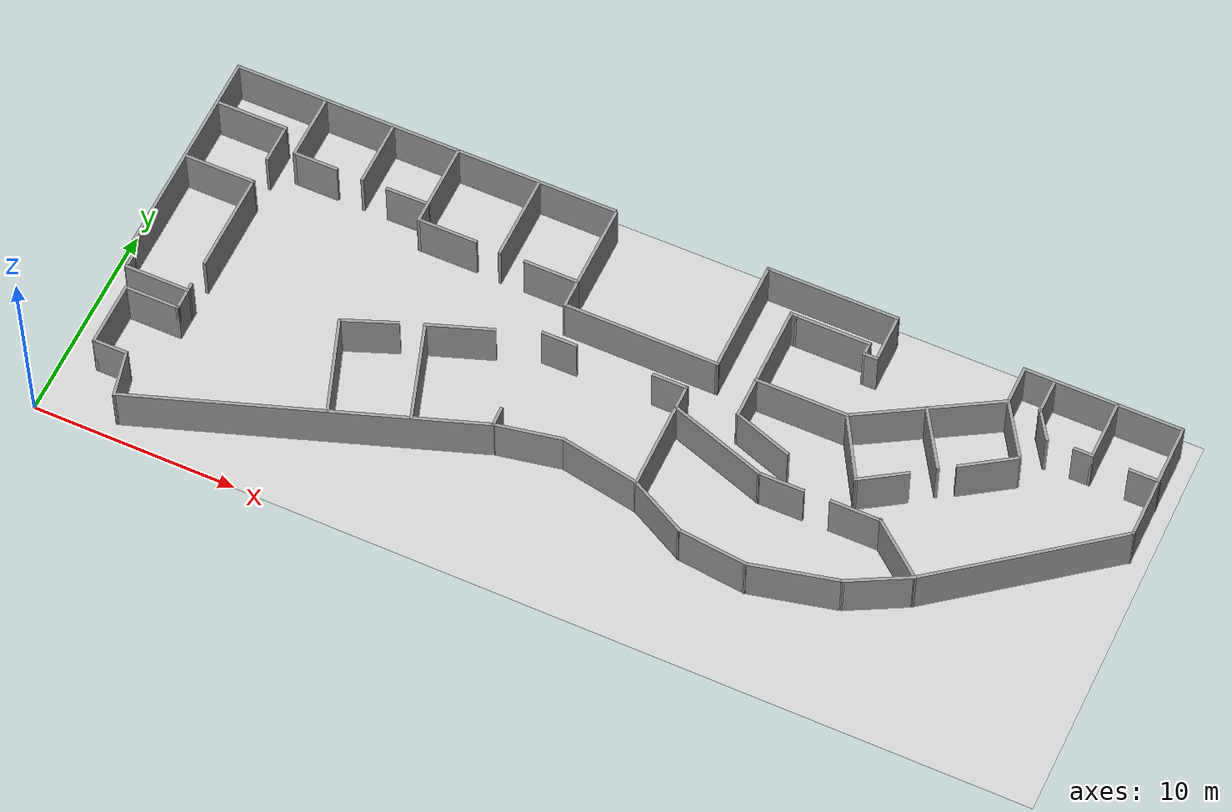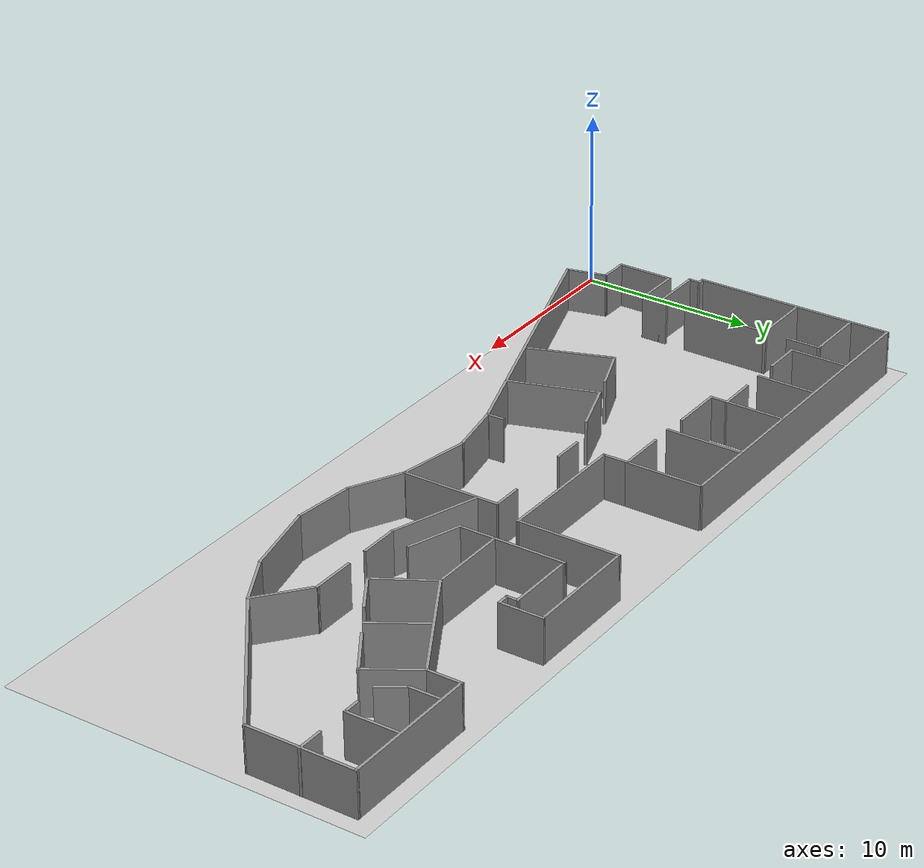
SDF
<sdf version='1.7'>
  <world name='carpet world'>
    <model name='office_carpet'>
      <static>1</static>
      <link name='link'>
        <pose>24.25 10 0 0 -0 0</pose>
        <collision name='collision'>
          <geometry>
            <plane>
              <normal>0 0 1</normal>
              <size>20 20</size>
            </plane>
          </geometry>
          <surface>
            <friction>
              <ode>
                <mu>100</mu>
                <mu2>50</mu2>
              </ode>
              <torsional>
                <ode/>
              </torsional>
            </friction>
            <contact>
              <ode/>
            </contact>
            <bounce/>
          </surface>
          <max_contacts>10</max_contacts>
        </collision>
        <visual name='visual'>
          <cast_shadows>0</cast_shadows>
          <geometry>
            <plane>
              <normal>0 0 1</normal>
              <size>48.5 20</size>
            </plane>
          </geometry>
          <material>
            <script>
              <uri>model://office_carpet/materials/scripts</uri>
              <uri>model://office_carpet/materials/textures</uri>
              <name>OfficeCarpet/Image</name>
            </script>
          </material>
        </visual>
        <self_collide>0</self_collide>
        <enable_wind>0</enable_wind>
        <kinematic>0</kinematic>
      </link>
    </model>
    <light name='sun' type='directional'>
      <cast_shadows>1</cast_shadows>
      <pose>0 0 10 0 -0 0</pose>
      <diffuse>0.8 0.8 0.8 1</diffuse>
      <specular>0.2 0.2 0.2 1</specular>
      <attenuation>
        <range>1000</range>
        <constant>0.9</constant>
        <linear>0.01</linear>
        <quadratic>0.001</quadratic>
      </attenuation>
      <direction>-0.5 0.1 -0.9</direction>
      <spot>
        <inner_angle>0</inner_angle>
        <outer_angle>0</outer_angle>
        <falloff>0</falloff>
      </spot>
    </light>
    <gui fullscreen='0'>
      <camera name='user_camera'>
        <pose>25.4342 9.4745 88.532 -2.8e-05 1.5698 1.56403</pose>
        <view_controller>ortho</view_controller>
        <projection_type>orthographic</projection_type>
      </camera>
    </gui>
    <scene>
      <grid>0</grid>
      <ambient>0.4 0.4 0.4 1</ambient>
      <background>0.7 0.7 0.7 1</background>
      <shadows>1</shadows>
    </scene>
    <gravity>0 0 -9.8</gravity>
    <magnetic_field>6e-06 2.3e-05 -4.2e-05</magnetic_field>
    <atmosphere type='adiabatic'/>
    <physics type='ode'>
      <max_step_size>0.001</max_step_size>
      <real_time_factor>1</real_time_factor>
      <real_time_update_rate>1000</real_time_update_rate>
    </physics>
    <wind/>
    <spherical_coordinates>
      <surface_model>EARTH_WGS84</surface_model>
      <latitude_deg>0</latitude_deg>
      <longitude_deg>0</longitude_deg>
      <elevation>0</elevation>
      <heading_deg>0</heading_deg>
    </spherical_coordinates>
    <model name='Office'>
      <static>1</static>
      <pose>24.2388 9.95234 0 0 -0 0</pose>
      <link name='Wall_0'>
        <collision name='Wall_0_Collision'>
          <geometry>
            <box>
              <size>1.5 0.15 2.5</size>
            </box>
          </geometry>
          <pose>0 0 1.25 0 -0 0</pose>
          <max_contacts>10</max_contacts>
          <surface>
            <contact>
              <ode/>
            </contact>
            <bounce/>
            <friction>
              <torsional>
                <ode/>
              </torsional>
              <ode/>
            </friction>
          </surface>
        </collision>
        <visual name='Wall_0_Visual'>
          <pose>0 0 1.25 0 -0 0</pose>
          <geometry>
            <box>
              <size>1.5 0.15 2.5</size>
            </box>
          </geometry>
          <material>
            <script>
              <uri>file://media/materials/scripts/gazebo.material</uri>
              <name>Gazebo/Grey</name>
            </script>
            <ambient>1 1 1 1</ambient>
          </material>
          <meta>
            <layer>0</layer>
          </meta>
        </visual>
        <pose>-19.9946 -3.18864 0 0 -0 1.5708</pose>
        <self_collide>0</self_collide>
        <enable_wind>0</enable_wind>
        <kinematic>0</kinematic>
      </link>
      <link name='Wall_100'>
        <collision name='Wall_100_Collision'>
          <geometry>
            <box>
              <size>4.46792 0.15 2.5</size>
            </box>
          </geometry>
          <pose>0 0 1.25 0 -0 0</pose>
          <max_contacts>10</max_contacts>
          <surface>
            <contact>
              <ode/>
            </contact>
            <bounce/>
            <friction>
              <torsional>
                <ode/>
              </torsional>
              <ode/>
            </friction>
          </surface>
        </collision>
        <visual name='Wall_100_Visual'>
          <pose>0 0 1.25 0 -0 0</pose>
          <geometry>
            <box>
              <size>4.46792 0.15 2.5</size>
            </box>
          </geometry>
          <material>
            <script>
              <uri>file://media/materials/scripts/gazebo.material</uri>
              <name>Gazebo/Grey</name>
            </script>
            <ambient>1 1 1 1</ambient>
          </material>
          <meta>
            <layer>0</layer>
          </meta>
        </visual>
        <pose>10.6963 -4.85422 0 0 -0 0.228635</pose>
        <self_collide>0</self_collide>
        <enable_wind>0</enable_wind>
        <kinematic>0</kinematic>
      </link>
      <link name='Wall_101'>
        <collision name='Wall_101_Collision'>
          <geometry>
            <box>
              <size>3.29755 0.15 2.5</size>
            </box>
          </geometry>
          <pose>0 0 1.25 0 -0 0</pose>
          <max_contacts>10</max_contacts>
          <surface>
            <contact>
              <ode/>
            </contact>
            <bounce/>
            <friction>
              <torsional>
                <ode/>
              </torsional>
              <ode/>
            </friction>
          </surface>
        </collision>
        <visual name='Wall_101_Visual'>
          <pose>0 0 1.25 0 -0 0</pose>
          <geometry>
            <box>
              <size>3.29755 0.15 2.5</size>
            </box>
          </geometry>
          <material>
            <script>
              <uri>file://media/materials/scripts/gazebo.material</uri>
              <name>Gazebo/Grey</name>
            </script>
            <ambient>1 1 1 1</ambient>
          </material>
          <meta>
            <layer>0</layer>
          </meta>
        </visual>
        <pose>14.1877 -3.6243 0 0 -0 0.489957</pose>
        <self_collide>0</self_collide>
        <enable_wind>0</enable_wind>
        <kinematic>0</kinematic>
      </link>
      <link name='Wall_103'>
        <collision name='Wall_103_Collision'>
          <geometry>
            <box>
              <size>7.38394 0.15 2.5</size>
            </box>
          </geometry>
          <pose>0 0 1.25 0 -0 0</pose>
          <max_contacts>10</max_contacts>
          <surface>
            <contact>
              <ode/>
            </contact>
            <bounce/>
            <friction>
              <torsional>
                <ode/>
              </torsional>
              <ode/>
            </friction>
          </surface>
        </collision>
        <visual name='Wall_103_Visual'>
          <pose>0 0 1.25 0 -0 0</pose>
          <geometry>
            <box>
              <size>7.38394 0.15 2.5</size>
            </box>
          </geometry>
          <material>
            <script>
              <uri>file://media/materials/scripts/gazebo.material</uri>
              <name>Gazebo/Grey</name>
            </script>
            <ambient>1 1 1 1</ambient>
          </material>
          <meta>
            <layer>0</layer>
          </meta>
        </visual>
        <pose>12.6994 5.35548 0 0 -0 0.533135</pose>
        <self_collide>0</self_collide>
        <enable_wind>0</enable_wind>
        <kinematic>0</kinematic>
      </link>
      <link name='Wall_104'>
        <collision name='Wall_104_Collision'>
          <geometry>
            <box>
              <size>2 0.15 2.5</size>
            </box>
          </geometry>
          <pose>0 0 1.25 0 -0 0</pose>
          <max_contacts>10</max_contacts>
          <surface>
            <contact>
              <ode/>
            </contact>
            <bounce/>
            <friction>
              <torsional>
                <ode/>
              </torsional>
              <ode/>
            </friction>
          </surface>
        </collision>
        <visual name='Wall_104_Visual'>
          <pose>0 0 1.25 0 -0 0</pose>
          <geometry>
            <box>
              <size>2 0.15 2.5</size>
            </box>
          </geometry>
          <material>
            <script>
              <uri>file://media/materials/scripts/gazebo.material</uri>
              <name>Gazebo/Grey</name>
            </script>
            <ambient>1 1 1 1</ambient>
          </material>
          <meta>
            <layer>0</layer>
          </meta>
        </visual>
        <pose>15.8144 8.11875 0 0 -0 1.5708</pose>
        <self_collide>0</self_collide>
        <enable_wind>0</enable_wind>
        <kinematic>0</kinematic>
      </link>
      <link name='Wall_105'>
        <collision name='Wall_105_Collision'>
          <geometry>
            <box>
              <size>7.75 0.15 2.5</size>
            </box>
          </geometry>
          <pose>0 0 1.25 0 -0 0</pose>
          <max_contacts>10</max_contacts>
          <surface>
            <contact>
              <ode/>
            </contact>
            <bounce/>
            <friction>
              <torsional>
                <ode/>
              </torsional>
              <ode/>
            </friction>
          </surface>
        </collision>
        <visual name='Wall_105_Visual'>
          <pose>0 0 1.25 0 -0 0</pose>
          <geometry>
            <box>
              <size>7.75 0.15 2.5</size>
            </box>
          </geometry>
          <material>
            <script>
              <uri>file://media/materials/scripts/gazebo.material</uri>
              <name>Gazebo/Grey</name>
            </script>
            <ambient>1 1 1 1</ambient>
          </material>
          <meta>
            <layer>0</layer>
          </meta>
        </visual>
        <pose>19.6144 9.04375 0 0 -0 0</pose>
        <self_collide>0</self_collide>
        <enable_wind>0</enable_wind>
        <kinematic>0</kinematic>
      </link>
      <link name='Wall_106'>
        <collision name='Wall_106_Collision'>
          <geometry>
            <box>
              <size>6 0.15 2.5</size>
            </box>
          </geometry>
          <pose>0 0 1.25 0 -0 0</pose>
          <max_contacts>10</max_contacts>
          <surface>
            <contact>
              <ode/>
            </contact>
            <bounce/>
            <friction>
              <torsional>
                <ode/>
              </torsional>
              <ode/>
            </friction>
          </surface>
        </collision>
        <visual name='Wall_106_Visual'>
          <pose>0 0 1.25 0 -0 0</pose>
          <geometry>
            <box>
              <size>6 0.15 2.5</size>
            </box>
          </geometry>
          <material>
            <script>
              <uri>file://media/materials/scripts/gazebo.material</uri>
              <name>Gazebo/Grey</name>
            </script>
            <ambient>1 1 1 1</ambient>
          </material>
          <meta>
            <layer>0</layer>
          </meta>
        </visual>
        <pose>23.4144 6.11875 0 0 -0 -1.5708</pose>
        <self_collide>0</self_collide>
        <enable_wind>0</enable_wind>
        <kinematic>0</kinematic>
      </link>
      <link name='Wall_107'>
        <collision name='Wall_107_Collision'>
          <geometry>
            <box>
              <size>10.0682 0.15 2.5</size>
            </box>
          </geometry>
          <pose>0 0 1.25 0 -0 0</pose>
          <max_contacts>10</max_contacts>
          <surface>
            <contact>
              <ode/>
            </contact>
            <bounce/>
            <friction>
              <torsional>
                <ode/>
              </torsional>
              <ode/>
            </friction>
          </surface>
        </collision>
        <visual name='Wall_107_Visual'>
          <pose>0 0 1.25 0 -0 0</pose>
          <geometry>
            <box>
              <size>10.0682 0.15 2.5</size>
            </box>
          </geometry>
          <material>
            <script>
              <uri>file://media/materials/scripts/gazebo.material</uri>
              <name>Gazebo/Grey</name>
            </script>
            <ambient>1 1 1 1</ambient>
          </material>
          <meta>
            <layer>0</layer>
          </meta>
        </visual>
        <pose>19.4954 0.155029 0 0 -0 -2.48205</pose>
        <self_collide>0</self_collide>
        <enable_wind>0</enable_wind>
        <kinematic>0</kinematic>
      </link>
      <link name='Wall_109'>
        <collision name='Wall_109_Collision'>
          <geometry>
            <box>
              <size>1.5 0.15 2.5</size>
            </box>
          </geometry>
          <pose>0 0 1.25 0 -0 0</pose>
          <max_contacts>10</max_contacts>
          <surface>
            <contact>
              <ode/>
            </contact>
            <bounce/>
            <friction>
              <torsional>
                <ode/>
              </torsional>
              <ode/>
            </friction>
          </surface>
        </collision>
        <visual name='Wall_109_Visual'>
          <pose>0 0 1.25 0 -0 0</pose>
          <geometry>
            <box>
              <size>1.5 0.15 2.5</size>
            </box>
          </geometry>
          <material>
            <script>
              <uri>file://media/materials/scripts/gazebo.material</uri>
              <name>Gazebo/Grey</name>
            </script>
            <ambient>1 1 1 1</ambient>
          </material>
          <meta>
            <layer>0</layer>
          </meta>
        </visual>
        <pose>22.757 6.13575 0 0 -0 3.14159</pose>
        <self_collide>0</self_collide>
        <enable_wind>0</enable_wind>
        <kinematic>0</kinematic>
      </link>
      <link name='Wall_11'>
        <collision name='Wall_11_Collision'>
          <geometry>
            <box>
              <size>2 0.15 2.5</size>
            </box>
          </geometry>
          <pose>0 0 1.25 0 -0 0</pose>
          <max_contacts>10</max_contacts>
          <surface>
            <contact>
              <ode/>
            </contact>
            <bounce/>
            <friction>
              <torsional>
                <ode/>
              </torsional>
              <ode/>
            </friction>
          </surface>
        </collision>
        <visual name='Wall_11_Visual'>
          <pose>0 0 1.25 0 -0 0</pose>
          <geometry>
            <box>
              <size>2 0.15 2.5</size>
            </box>
          </geometry>
          <material>
            <script>
              <uri>file://media/materials/scripts/gazebo.material</uri>
              <name>Gazebo/Grey</name>
            </script>
            <ambient>1 1 1 1</ambient>
          </material>
          <meta>
            <layer>0</layer>
          </meta>
        </visual>
        <pose>-19.9418 5.9961 0 0 -0 1.5708</pose>
        <self_collide>0</self_collide>
        <enable_wind>0</enable_wind>
        <kinematic>0</kinematic>
      </link>
      <link name='Wall_111'>
        <collision name='Wall_111_Collision'>
          <geometry>
            <box>
              <size>3 0.15 2.5</size>
            </box>
          </geometry>
          <pose>0 0 1.25 0 -0 0</pose>
          <max_contacts>10</max_contacts>
          <surface>
            <contact>
              <ode/>
            </contact>
            <bounce/>
            <friction>
              <torsional>
                <ode/>
              </torsional>
              <ode/>
            </friction>
          </surface>
        </collision>
        <visual name='Wall_111_Visual'>
          <pose>0 0 1.25 0 -0 0</pose>
          <geometry>
            <box>
              <size>3 0.15 2.5</size>
            </box>
          </geometry>
          <material>
            <script>
              <uri>file://media/materials/scripts/gazebo.material</uri>
              <name>Gazebo/Grey</name>
            </script>
            <ambient>1 1 1 1</ambient>
          </material>
          <meta>
            <layer>0</layer>
          </meta>
        </visual>
        <pose>20.2844 7.56075 0 0 -0 1.5708</pose>
        <self_collide>0</self_collide>
        <enable_wind>0</enable_wind>
        <kinematic>0</kinematic>
      </link>
      <link name='Wall_113'>
        <collision name='Wall_113_Collision'>
          <geometry>
            <box>
              <size>1 0.15 2.5</size>
            </box>
          </geometry>
          <pose>0 0 1.25 0 -0 0</pose>
          <max_contacts>10</max_contacts>
          <surface>
            <contact>
              <ode/>
            </contact>
            <bounce/>
            <friction>
              <torsional>
                <ode/>
              </torsional>
              <ode/>
            </friction>
          </surface>
        </collision>
        <visual name='Wall_113_Visual'>
          <pose>0 0 1.25 0 -0 0</pose>
          <geometry>
            <box>
              <size>1 0.15 2.5</size>
            </box>
          </geometry>
          <material>
            <script>
              <uri>file://media/materials/scripts/gazebo.material</uri>
              <name>Gazebo/Grey</name>
            </script>
            <ambient>1 1 1 1</ambient>
          </material>
          <meta>
            <layer>0</layer>
          </meta>
        </visual>
        <pose>19.8594 6.13575 0 0 -0 3.14159</pose>
        <self_collide>0</self_collide>
        <enable_wind>0</enable_wind>
        <kinematic>0</kinematic>
      </link>
      <link name='Wall_115'>
        <collision name='Wall_115_Collision'>
          <geometry>
            <box>
              <size>1.63921 0.15 2.5</size>
            </box>
          </geometry>
          <pose>0 0 1.25 0 -0 0</pose>
          <max_contacts>10</max_contacts>
          <surface>
            <contact>
              <ode/>
            </contact>
            <bounce/>
            <friction>
              <torsional>
                <ode/>
              </torsional>
              <ode/>
            </friction>
          </surface>
        </collision>
        <visual name='Wall_115_Visual'>
          <pose>0 0 1.25 0 -0 0</pose>
          <geometry>
            <box>
              <size>1.63921 0.15 2.5</size>
            </box>
          </geometry>
          <material>
            <script>
              <uri>file://media/materials/scripts/gazebo.material</uri>
              <name>Gazebo/Grey</name>
            </script>
            <ambient>1 1 1 1</ambient>
          </material>
          <meta>
            <layer>0</layer>
          </meta>
        </visual>
        <pose>17.7056 6.70443 0 0 -0 2.15387</pose>
        <self_collide>0</self_collide>
        <enable_wind>0</enable_wind>
        <kinematic>0</kinematic>
      </link>
      <link name='Wall_116'>
        <collision name='Wall_116_Collision'>
          <geometry>
            <box>
              <size>1.75 0.15 2.5</size>
            </box>
          </geometry>
          <pose>0 0 1.25 0 -0 0</pose>
          <max_contacts>10</max_contacts>
          <surface>
            <contact>
              <ode/>
            </contact>
            <bounce/>
            <friction>
              <torsional>
                <ode/>
              </torsional>
              <ode/>
            </friction>
          </surface>
        </collision>
        <visual name='Wall_116_Visual'>
          <pose>0 0 1.25 0 -0 0</pose>
          <geometry>
            <box>
              <size>1.75 0.15 2.5</size>
            </box>
          </geometry>
          <material>
            <script>
              <uri>file://media/materials/scripts/gazebo.material</uri>
              <name>Gazebo/Grey</name>
            </script>
            <ambient>1 1 1 1</ambient>
          </material>
          <meta>
            <layer>0</layer>
          </meta>
        </visual>
        <pose>17.2956 8.126 0 0 -0 1.5708</pose>
        <self_collide>0</self_collide>
        <enable_wind>0</enable_wind>
        <kinematic>0</kinematic>
      </link>
      <link name='Wall_120'>
        <collision name='Wall_120_Collision'>
          <geometry>
            <box>
              <size>3.12195 0.15 2.5</size>
            </box>
          </geometry>
          <pose>0 0 1.25 0 -0 0</pose>
          <max_contacts>10</max_contacts>
          <surface>
            <contact>
              <ode/>
            </contact>
            <bounce/>
            <friction>
              <torsional>
                <ode/>
              </torsional>
              <ode/>
            </friction>
          </surface>
        </collision>
        <visual name='Wall_120_Visual'>
          <pose>0 0 1.25 0 -0 0</pose>
          <geometry>
            <box>
              <size>3.12195 0.15 2.5</size>
            </box>
          </geometry>
          <material>
            <script>
              <uri>file://media/materials/scripts/gazebo.material</uri>
              <name>Gazebo/Grey</name>
            </script>
            <ambient>1 1 1 1</ambient>
          </material>
          <meta>
            <layer>0</layer>
          </meta>
        </visual>
        <pose>16.6079 5.93738 0 0 -0 -1.00748</pose>
        <self_collide>0</self_collide>
        <enable_wind>0</enable_wind>
        <kinematic>0</kinematic>
      </link>
      <link name='Wall_121'>
        <collision name='Wall_121_Collision'>
          <geometry>
            <box>
              <size>2.91564 0.15 2.5</size>
            </box>
          </geometry>
          <pose>0 0 1.25 0 -0 0</pose>
          <max_contacts>10</max_contacts>
          <surface>
            <contact>
              <ode/>
            </contact>
            <bounce/>
            <friction>
              <torsional>
                <ode/>
              </torsional>
              <ode/>
            </friction>
          </surface>
        </collision>
        <visual name='Wall_121_Visual'>
          <pose>0 0 1.25 0 -0 0</pose>
          <geometry>
            <box>
              <size>2.91564 0.15 2.5</size>
            </box>
          </geometry>
          <material>
            <script>
              <uri>file://media/materials/scripts/gazebo.material</uri>
              <name>Gazebo/Grey</name>
            </script>
            <ambient>1 1 1 1</ambient>
          </material>
          <meta>
            <layer>0</layer>
          </meta>
        </visual>
        <pose>16.2508 3.91395 0 0 -0 -2.55359</pose>
        <self_collide>0</self_collide>
        <enable_wind>0</enable_wind>
        <kinematic>0</kinematic>
      </link>
      <link name='Wall_123'>
        <collision name='Wall_123_Collision'>
          <geometry>
            <box>
              <size>3.23967 0.15 2.5</size>
            </box>
          </geometry>
          <pose>0 0 1.25 0 -0 0</pose>
          <max_contacts>10</max_contacts>
          <surface>
            <contact>
              <ode/>
            </contact>
            <bounce/>
            <friction>
              <torsional>
                <ode/>
              </torsional>
              <ode/>
            </friction>
          </surface>
        </collision>
        <visual name='Wall_123_Visual'>
          <pose>0 0 1.25 0 -0 0</pose>
          <geometry>
            <box>
              <size>3.23967 0.15 2.5</size>
            </box>
          </geometry>
          <material>
            <script>
              <uri>file://media/materials/scripts/gazebo.material</uri>
              <name>Gazebo/Grey</name>
            </script>
            <ambient>1 1 1 1</ambient>
          </material>
          <meta>
            <layer>0</layer>
          </meta>
        </visual>
        <pose>13.4868 4.00653 0 0 -0 -1.01129</pose>
        <self_collide>0</self_collide>
        <enable_wind>0</enable_wind>
        <kinematic>0</kinematic>
      </link>
      <link name='Wall_125'>
        <collision name='Wall_125_Collision'>
          <geometry>
            <box>
              <size>2.51976 0.15 2.5</size>
            </box>
          </geometry>
          <pose>0 0 1.25 0 -0 0</pose>
          <max_contacts>10</max_contacts>
          <surface>
            <contact>
              <ode/>
            </contact>
            <bounce/>
            <friction>
              <torsional>
                <ode/>
              </torsional>
              <ode/>
            </friction>
          </surface>
        </collision>
        <visual name='Wall_125_Visual'>
          <pose>0 0 1.25 0 -0 0</pose>
          <geometry>
            <box>
              <size>2.51976 0.15 2.5</size>
            </box>
          </geometry>
          <material>
            <script>
              <uri>file://media/materials/scripts/gazebo.material</uri>
              <name>Gazebo/Grey</name>
            </script>
            <ambient>1 1 1 1</ambient>
          </material>
          <meta>
            <layer>0</layer>
          </meta>
        </visual>
        <pose>12.2541 1.25989 0 0 -0 0.574485</pose>
        <self_collide>0</self_collide>
        <enable_wind>0</enable_wind>
        <kinematic>0</kinematic>
      </link>
      <link name='Wall_18'>
        <collision name='Wall_18_Collision'>
          <geometry>
            <box>
              <size>2.75 0.15 2.5</size>
            </box>
          </geometry>
          <pose>0 0 1.25 0 -0 0</pose>
          <max_contacts>10</max_contacts>
          <surface>
            <contact>
              <ode/>
            </contact>
            <bounce/>
            <friction>
              <torsional>
                <ode/>
              </torsional>
              <ode/>
            </friction>
          </surface>
        </collision>
        <visual name='Wall_18_Visual'>
          <pose>0 0 1.25 0 -0 0</pose>
          <geometry>
            <box>
              <size>2.75 0.15 2.5</size>
            </box>
          </geometry>
          <material>
            <script>
              <uri>file://media/materials/scripts/gazebo.material</uri>
              <name>Gazebo/Grey</name>
            </script>
            <ambient>1 1 1 1</ambient>
          </material>
          <meta>
            <layer>0</layer>
          </meta>
        </visual>
        <pose>-21.2946 -3.86364 0 0 -0 3.14159</pose>
        <self_collide>0</self_collide>
        <enable_wind>0</enable_wind>
        <kinematic>0</kinematic>
      </link>
      <link name='Wall_19'>
        <collision name='Wall_19_Collision'>
          <geometry>
            <box>
              <size>3.25 0.15 2.5</size>
            </box>
          </geometry>
          <pose>0 0 1.25 0 -0 0</pose>
          <max_contacts>10</max_contacts>
          <surface>
            <contact>
              <ode/>
            </contact>
            <bounce/>
            <friction>
              <torsional>
                <ode/>
              </torsional>
              <ode/>
            </friction>
          </surface>
        </collision>
        <visual name='Wall_19_Visual'>
          <pose>0 0 1.25 0 -0 0</pose>
          <geometry>
            <box>
              <size>3.25 0.15 2.5</size>
            </box>
          </geometry>
          <material>
            <script>
              <uri>file://media/materials/scripts/gazebo.material</uri>
              <name>Gazebo/Grey</name>
            </script>
            <ambient>1 1 1 1</ambient>
          </material>
          <meta>
            <layer>0</layer>
          </meta>
        </visual>
        <pose>-22.5946 -5.41364 0 0 -0 -1.5708</pose>
        <self_collide>0</self_collide>
        <enable_wind>0</enable_wind>
        <kinematic>0</kinematic>
      </link>
      <link name='Wall_2'>
        <collision name='Wall_2_Collision'>
          <geometry>
            <box>
              <size>3.25 0.15 2.5</size>
            </box>
          </geometry>
          <pose>0 0 1.25 0 -0 0</pose>
          <max_contacts>10</max_contacts>
          <surface>
            <contact>
              <ode/>
            </contact>
            <bounce/>
            <friction>
              <torsional>
                <ode/>
              </torsional>
              <ode/>
            </friction>
          </surface>
        </collision>
        <visual name='Wall_2_Visual'>
          <pose>0 0 1.25 0 -0 0</pose>
          <geometry>
            <box>
              <size>3.25 0.15 2.5</size>
            </box>
          </geometry>
          <material>
            <script>
              <uri>file://media/materials/scripts/gazebo.material</uri>
              <name>Gazebo/Grey</name>
            </script>
            <ambient>1 1 1 1</ambient>
          </material>
          <meta>
            <layer>0</layer>
          </meta>
        </visual>
        <pose>-21.5446 -2.84921 0 0 -0 3.14159</pose>
        <self_collide>0</self_collide>
        <enable_wind>0</enable_wind>
        <kinematic>0</kinematic>
      </link>
      <link name='Wall_23'>
        <collision name='Wall_23_Collision'>
          <geometry>
            <box>
              <size>1.75 0.15 2.5</size>
            </box>
          </geometry>
          <pose>0 0 1.25 0 -0 0</pose>
          <max_contacts>10</max_contacts>
          <surface>
            <contact>
              <ode/>
            </contact>
            <bounce/>
            <friction>
              <torsional>
                <ode/>
              </torsional>
              <ode/>
            </friction>
          </surface>
        </collision>
        <visual name='Wall_23_Visual'>
          <pose>0 0 1.25 0 -0 0</pose>
          <geometry>
            <box>
              <size>1.75 0.15 2.5</size>
            </box>
          </geometry>
          <material>
            <script>
              <uri>file://media/materials/scripts/gazebo.material</uri>
              <name>Gazebo/Grey</name>
            </script>
            <ambient>1 1 1 1</ambient>
          </material>
          <meta>
            <layer>0</layer>
          </meta>
        </visual>
        <pose>-21.7946 -6.96364 0 0 -0 0</pose>
        <self_collide>0</self_collide>
        <enable_wind>0</enable_wind>
        <kinematic>0</kinematic>
      </link>
      <link name='Wall_24'>
        <collision name='Wall_24_Collision'>
          <geometry>
            <box>
              <size>2.3739 0.15 2.5</size>
            </box>
          </geometry>
          <pose>0 0 1.25 0 -0 0</pose>
          <max_contacts>10</max_contacts>
          <surface>
            <contact>
              <ode/>
            </contact>
            <bounce/>
            <friction>
              <torsional>
                <ode/>
              </torsional>
              <ode/>
            </friction>
          </surface>
        </collision>
        <visual name='Wall_24_Visual'>
          <pose>0 0 1.25 0 -0 0</pose>
          <geometry>
            <box>
              <size>2.3739 0.15 2.5</size>
            </box>
          </geometry>
          <material>
            <script>
              <uri>file://media/materials/scripts/gazebo.material</uri>
              <name>Gazebo/Grey</name>
            </script>
            <ambient>1 1 1 1</ambient>
          </material>
          <meta>
            <layer>0</layer>
          </meta>
        </visual>
        <pose>-20.7369 -8.0453 0 0 -0 -1.33685</pose>
        <self_collide>0</self_collide>
        <enable_wind>0</enable_wind>
        <kinematic>0</kinematic>
      </link>
      <link name='Wall_25'>
        <collision name='Wall_25_Collision'>
          <geometry>
            <box>
              <size>17.14 0.15 2.5</size>
            </box>
          </geometry>
          <pose>0 0 1.25 0 -0 0</pose>
          <max_contacts>10</max_contacts>
          <surface>
            <contact>
              <ode/>
            </contact>
            <bounce/>
            <friction>
              <torsional>
                <ode/>
              </torsional>
              <ode/>
            </friction>
          </surface>
        </collision>
        <visual name='Wall_25_Visual'>
          <pose>0 0 1.25 0 -0 0</pose>
          <geometry>
            <box>
              <size>17.14 0.15 2.5</size>
            </box>
          </geometry>
          <material>
            <script>
              <uri>file://media/materials/scripts/gazebo.material</uri>
              <name>Gazebo/Grey</name>
            </script>
            <ambient>1 1 1 1</ambient>
          </material>
          <meta>
            <layer>0</layer>
          </meta>
        </visual>
        <pose>-12.4647 -6.31004 0 0 -0 0.337997</pose>
        <self_collide>0</self_collide>
        <enable_wind>0</enable_wind>
        <kinematic>0</kinematic>
      </link>
      <link name='Wall_26'>
        <collision name='Wall_26_Collision'>
          <geometry>
            <box>
              <size>3.32984 0.15 2.5</size>
            </box>
          </geometry>
          <pose>0 0 1.25 0 -0 0</pose>
          <max_contacts>10</max_contacts>
          <surface>
            <contact>
              <ode/>
            </contact>
            <bounce/>
            <friction>
              <torsional>
                <ode/>
              </torsional>
              <ode/>
            </friction>
          </surface>
        </collision>
        <visual name='Wall_26_Visual'>
          <pose>0 0 1.25 0 -0 0</pose>
          <geometry>
            <box>
              <size>3.32984 0.15 2.5</size>
            </box>
          </geometry>
          <material>
            <script>
              <uri>file://media/materials/scripts/gazebo.material</uri>
              <name>Gazebo/Grey</name>
            </script>
            <ambient>1 1 1 1</ambient>
          </material>
          <meta>
            <layer>0</layer>
          </meta>
        </visual>
        <pose>-2.88984 -3.18894 0 0 -0 0.192502</pose>
        <self_collide>0</self_collide>
        <enable_wind>0</enable_wind>
        <kinematic>0</kinematic>
      </link>
      <link name='Wall_28'>
        <collision name='Wall_28_Collision'>
          <geometry>
            <box>
              <size>4.07246 0.15 2.5</size>
            </box>
          </geometry>
          <pose>0 0 1.25 0 -0 0</pose>
          <max_contacts>10</max_contacts>
          <surface>
            <contact>
              <ode/>
            </contact>
            <bounce/>
            <friction>
              <torsional>
                <ode/>
              </torsional>
              <ode/>
            </friction>
          </surface>
        </collision>
        <visual name='Wall_28_Visual'>
          <pose>0 0 1.25 0 -0 0</pose>
          <geometry>
            <box>
              <size>4.07246 0.15 2.5</size>
            </box>
          </geometry>
          <material>
            <script>
              <uri>file://media/materials/scripts/gazebo.material</uri>
              <name>Gazebo/Grey</name>
            </script>
            <ambient>1 1 1 1</ambient>
          </material>
          <meta>
            <layer>0</layer>
          </meta>
        </visual>
        <pose>0.601556 -3.22861 0 0 -0 -0.176235</pose>
        <self_collide>0</self_collide>
        <enable_wind>0</enable_wind>
        <kinematic>0</kinematic>
      </link>
      <link name='Wall_3'>
        <collision name='Wall_3_Collision'>
          <geometry>
            <box>
              <size>0.75 0.15 2.5</size>
            </box>
          </geometry>
          <pose>0 0 1.25 0 -0 0</pose>
          <max_contacts>10</max_contacts>
          <surface>
            <contact>
              <ode/>
            </contact>
            <bounce/>
            <friction>
              <torsional>
                <ode/>
              </torsional>
              <ode/>
            </friction>
          </surface>
        </collision>
        <visual name='Wall_3_Visual'>
          <pose>0 0 1.25 0 -0 0</pose>
          <geometry>
            <box>
              <size>0.75 0.15 2.5</size>
            </box>
          </geometry>
          <material>
            <script>
              <uri>file://media/materials/scripts/gazebo.material</uri>
              <name>Gazebo/Grey</name>
            </script>
            <ambient>1 1 1 1</ambient>
          </material>
          <meta>
            <layer>0</layer>
          </meta>
        </visual>
        <pose>-23.0946 -2.54921 0 0 -0 1.5708</pose>
        <self_collide>0</self_collide>
        <enable_wind>0</enable_wind>
        <kinematic>0</kinematic>
      </link>
      <link name='Wall_30'>
        <collision name='Wall_30_Collision'>
          <geometry>
            <box>
              <size>1.02285 0.15 2.5</size>
            </box>
          </geometry>
          <pose>0 0 1.25 0 -0 0</pose>
          <max_contacts>10</max_contacts>
          <surface>
            <contact>
              <ode/>
            </contact>
            <bounce/>
            <friction>
              <torsional>
                <ode/>
              </torsional>
              <ode/>
            </friction>
          </surface>
        </collision>
        <visual name='Wall_30_Visual'>
          <pose>0 0 1.25 0 -0 0</pose>
          <geometry>
            <box>
              <size>1.02285 0.15 2.5</size>
            </box>
          </geometry>
          <material>
            <script>
              <uri>file://media/materials/scripts/gazebo.material</uri>
              <name>Gazebo/Grey</name>
            </script>
            <ambient>1 1 1 1</ambient>
          </material>
          <meta>
            <layer>0</layer>
          </meta>
        </visual>
        <pose>-4.49007 -3.05669 0 0 -0 -1.5405</pose>
        <self_collide>0</self_collide>
        <enable_wind>0</enable_wind>
        <kinematic>0</kinematic>
      </link>
      <link name='Wall_32'>
        <collision name='Wall_32_Collision'>
          <geometry>
            <box>
              <size>5.05981 0.15 2.5</size>
            </box>
          </geometry>
          <pose>0 0 1.25 0 -0 0</pose>
          <max_contacts>10</max_contacts>
          <surface>
            <contact>
              <ode/>
            </contact>
            <bounce/>
            <friction>
              <torsional>
                <ode/>
              </torsional>
              <ode/>
            </friction>
          </surface>
        </collision>
        <visual name='Wall_32_Visual'>
          <pose>0 0 1.25 0 -0 0</pose>
          <geometry>
            <box>
              <size>5.05981 0.15 2.5</size>
            </box>
          </geometry>
          <material>
            <script>
              <uri>file://media/materials/scripts/gazebo.material</uri>
              <name>Gazebo/Grey</name>
            </script>
            <ambient>1 1 1 1</ambient>
          </material>
          <meta>
            <layer>0</layer>
          </meta>
        </visual>
        <pose>-8.72207 -2.35576 0 0 -0 1.89425</pose>
        <self_collide>0</self_collide>
        <enable_wind>0</enable_wind>
        <kinematic>0</kinematic>
      </link>
      <link name='Wall_33'>
        <collision name='Wall_33_Collision'>
          <geometry>
            <box>
              <size>3.27076 0.15 2.5</size>
            </box>
          </geometry>
          <pose>0 0 1.25 0 -0 0</pose>
          <max_contacts>10</max_contacts>
          <surface>
            <contact>
              <ode/>
            </contact>
            <bounce/>
            <friction>
              <torsional>
                <ode/>
              </torsional>
              <ode/>
            </friction>
          </surface>
        </collision>
        <visual name='Wall_33_Visual'>
          <pose>0 0 1.25 0 -0 0</pose>
          <geometry>
            <box>
              <size>3.27076 0.15 2.5</size>
            </box>
          </geometry>
          <material>
            <script>
              <uri>file://media/materials/scripts/gazebo.material</uri>
              <name>Gazebo/Grey</name>
            </script>
            <ambient>1 1 1 1</ambient>
          </material>
          <meta>
            <layer>0</layer>
          </meta>
        </visual>
        <pose>-8.03437 0.500839 0 0 -0 0.345875</pose>
        <self_collide>0</self_collide>
        <enable_wind>0</enable_wind>
        <kinematic>0</kinematic>
      </link>
      <link name='Wall_35'>
        <collision name='Wall_35_Collision'>
          <geometry>
            <box>
              <size>1.75 0.15 2.5</size>
            </box>
          </geometry>
          <pose>0 0 1.25 0 -0 0</pose>
          <max_contacts>10</max_contacts>
          <surface>
            <contact>
              <ode/>
            </contact>
            <bounce/>
            <friction>
              <torsional>
                <ode/>
              </torsional>
              <ode/>
            </friction>
          </surface>
        </collision>
        <visual name='Wall_35_Visual'>
          <pose>0 0 1.25 0 -0 0</pose>
          <geometry>
            <box>
              <size>1.75 0.15 2.5</size>
            </box>
          </geometry>
          <material>
            <script>
              <uri>file://media/materials/scripts/gazebo.material</uri>
              <name>Gazebo/Grey</name>
            </script>
            <ambient>1 1 1 1</ambient>
          </material>
          <meta>
            <layer>0</layer>
          </meta>
        </visual>
        <pose>-3.70329 1.79689 0 0 -0 0</pose>
        <self_collide>0</self_collide>
        <enable_wind>0</enable_wind>
        <kinematic>0</kinematic>
      </link>
      <link name='Wall_37'>
        <collision name='Wall_37_Collision'>
          <geometry>
            <box>
              <size>1.75 0.15 2.5</size>
            </box>
          </geometry>
          <pose>0 0 1.25 0 -0 0</pose>
          <max_contacts>10</max_contacts>
          <surface>
            <contact>
              <ode/>
            </contact>
            <bounce/>
            <friction>
              <torsional>
                <ode/>
              </torsional>
              <ode/>
            </friction>
          </surface>
        </collision>
        <visual name='Wall_37_Visual'>
          <pose>0 0 1.25 0 -0 0</pose>
          <geometry>
            <box>
              <size>1.75 0.15 2.5</size>
            </box>
          </geometry>
          <material>
            <script>
              <uri>file://media/materials/scripts/gazebo.material</uri>
              <name>Gazebo/Grey</name>
            </script>
            <ambient>1 1 1 1</ambient>
          </material>
          <meta>
            <layer>0</layer>
          </meta>
        </visual>
        <pose>1.71896 1.84979 0 0 -0 0</pose>
        <self_collide>0</self_collide>
        <enable_wind>0</enable_wind>
        <kinematic>0</kinematic>
      </link>
      <link name='Wall_38'>
        <collision name='Wall_38_Collision'>
          <geometry>
            <box>
              <size>5.57227 0.15 2.5</size>
            </box>
          </geometry>
          <pose>0 0 1.25 0 -0 0</pose>
          <max_contacts>10</max_contacts>
          <surface>
            <contact>
              <ode/>
            </contact>
            <bounce/>
            <friction>
              <torsional>
                <ode/>
              </torsional>
              <ode/>
            </friction>
          </surface>
        </collision>
        <visual name='Wall_38_Visual'>
          <pose>0 0 1.25 0 -0 0</pose>
          <geometry>
            <box>
              <size>5.57227 0.15 2.5</size>
            </box>
          </geometry>
          <material>
            <script>
              <uri>file://media/materials/scripts/gazebo.material</uri>
              <name>Gazebo/Grey</name>
            </script>
            <ambient>1 1 1 1</ambient>
          </material>
          <meta>
            <layer>0</layer>
          </meta>
        </visual>
        <pose>2.52568 -0.861336 0 0 -0 -1.56832</pose>
        <self_collide>0</self_collide>
        <enable_wind>0</enable_wind>
        <kinematic>0</kinematic>
      </link>
      <link name='Wall_4'>
        <collision name='Wall_4_Collision'>
          <geometry>
            <box>
              <size>0.5 0.15 2.5</size>
            </box>
          </geometry>
          <pose>0 0 1.25 0 -0 0</pose>
          <max_contacts>10</max_contacts>
          <surface>
            <contact>
              <ode/>
            </contact>
            <bounce/>
            <friction>
              <torsional>
                <ode/>
              </torsional>
              <ode/>
            </friction>
          </surface>
        </collision>
        <visual name='Wall_4_Visual'>
          <pose>0 0 1.25 0 -0 0</pose>
          <geometry>
            <box>
              <size>0.5 0.15 2.5</size>
            </box>
          </geometry>
          <material>
            <script>
              <uri>file://media/materials/scripts/gazebo.material</uri>
              <name>Gazebo/Grey</name>
            </script>
            <ambient>1 1 1 1</ambient>
          </material>
          <meta>
            <layer>0</layer>
          </meta>
        </visual>
        <pose>-23.2696 -2.24921 0 0 -0 3.14159</pose>
        <self_collide>0</self_collide>
        <enable_wind>0</enable_wind>
        <kinematic>0</kinematic>
      </link>
      <link name='Wall_40'>
        <collision name='Wall_40_Collision'>
          <geometry>
            <box>
              <size>2.78729 0.15 2.5</size>
            </box>
          </geometry>
          <pose>0 0 1.25 0 -0 0</pose>
          <max_contacts>10</max_contacts>
          <surface>
            <contact>
              <ode/>
            </contact>
            <bounce/>
            <friction>
              <torsional>
                <ode/>
              </torsional>
              <ode/>
            </friction>
          </surface>
        </collision>
        <visual name='Wall_40_Visual'>
          <pose>0 0 1.25 0 -0 0</pose>
          <geometry>
            <box>
              <size>2.78729 0.15 2.5</size>
            </box>
          </geometry>
          <material>
            <script>
              <uri>file://media/materials/scripts/gazebo.material</uri>
              <name>Gazebo/Grey</name>
            </script>
            <ambient>1 1 1 1</ambient>
          </material>
          <meta>
            <layer>0</layer>
          </meta>
        </visual>
        <pose>-11.8735 -0.939152 0 0 -0 -2.76434</pose>
        <self_collide>0</self_collide>
        <enable_wind>0</enable_wind>
        <kinematic>0</kinematic>
      </link>
      <link name='Wall_41'>
        <collision name='Wall_41_Collision'>
          <geometry>
            <box>
              <size>4.92052 0.15 2.5</size>
            </box>
          </geometry>
          <pose>0 0 1.25 0 -0 0</pose>
          <max_contacts>10</max_contacts>
          <surface>
            <contact>
              <ode/>
            </contact>
            <bounce/>
            <friction>
              <torsional>
                <ode/>
              </torsional>
              <ode/>
            </friction>
          </surface>
        </collision>
        <visual name='Wall_41_Visual'>
          <pose>0 0 1.25 0 -0 0</pose>
          <geometry>
            <box>
              <size>4.92052 0.15 2.5</size>
            </box>
          </geometry>
          <material>
            <script>
              <uri>file://media/materials/scripts/gazebo.material</uri>
              <name>Gazebo/Grey</name>
            </script>
            <ambient>1 1 1 1</ambient>
          </material>
          <meta>
            <layer>0</layer>
          </meta>
        </visual>
        <pose>-12.2898 -3.66856 0 0 -0 -1.22451</pose>
        <self_collide>0</self_collide>
        <enable_wind>0</enable_wind>
        <kinematic>0</kinematic>
      </link>
      <link name='Wall_43'>
        <collision name='Wall_43_Collision'>
          <geometry>
            <box>
              <size>19.25 0.15 2.5</size>
            </box>
          </geometry>
          <pose>0 0 1.25 0 -0 0</pose>
          <max_contacts>10</max_contacts>
          <surface>
            <contact>
              <ode/>
            </contact>
            <bounce/>
            <friction>
              <torsional>
                <ode/>
              </torsional>
              <ode/>
            </friction>
          </surface>
        </collision>
        <visual name='Wall_43_Visual'>
          <pose>0 0 1.25 0 -0 0</pose>
          <geometry>
            <box>
              <size>19.25 0.15 2.5</size>
            </box>
          </geometry>
          <material>
            <script>
              <uri>file://media/materials/scripts/gazebo.material</uri>
              <name>Gazebo/Grey</name>
            </script>
            <ambient>1 1 1 1</ambient>
          </material>
          <meta>
            <layer>0</layer>
          </meta>
        </visual>
        <pose>-13.8946 9.10079 0 0 -0 0</pose>
        <self_collide>0</self_collide>
        <enable_wind>0</enable_wind>
        <kinematic>0</kinematic>
      </link>
      <link name='Wall_47'>
        <collision name='Wall_47_Collision'>
          <geometry>
            <box>
              <size>3.5 0.15 2.5</size>
            </box>
          </geometry>
          <pose>0 0 1.25 0 -0 0</pose>
          <max_contacts>10</max_contacts>
          <surface>
            <contact>
              <ode/>
            </contact>
            <bounce/>
            <friction>
              <torsional>
                <ode/>
              </torsional>
              <ode/>
            </friction>
          </surface>
        </collision>
        <visual name='Wall_47_Visual'>
          <pose>0 0 1.25 0 -0 0</pose>
          <geometry>
            <box>
              <size>3.5 0.15 2.5</size>
            </box>
          </geometry>
          <material>
            <script>
              <uri>file://media/materials/scripts/gazebo.material</uri>
              <name>Gazebo/Grey</name>
            </script>
            <ambient>1 1 1 1</ambient>
          </material>
          <meta>
            <layer>0</layer>
          </meta>
        </visual>
        <pose>-21.6168 6.9211 0 0 -0 3.14159</pose>
        <self_collide>0</self_collide>
        <enable_wind>0</enable_wind>
        <kinematic>0</kinematic>
      </link>
      <link name='Wall_49'>
        <collision name='Wall_49_Collision'>
          <geometry>
            <box>
              <size>2.25 0.15 2.5</size>
            </box>
          </geometry>
          <pose>0 0 1.25 0 -0 0</pose>
          <max_contacts>10</max_contacts>
          <surface>
            <contact>
              <ode/>
            </contact>
            <bounce/>
            <friction>
              <torsional>
                <ode/>
              </torsional>
              <ode/>
            </friction>
          </surface>
        </collision>
        <visual name='Wall_49_Visual'>
          <pose>0 0 1.25 0 -0 0</pose>
          <geometry>
            <box>
              <size>2.25 0.15 2.5</size>
            </box>
          </geometry>
          <material>
            <script>
              <uri>file://media/materials/scripts/gazebo.material</uri>
              <name>Gazebo/Grey</name>
            </script>
            <ambient>1 1 1 1</ambient>
          </material>
          <meta>
            <layer>0</layer>
          </meta>
        </visual>
        <pose>-17.8959 5.86728 0 0 -0 0</pose>
        <self_collide>0</self_collide>
        <enable_wind>0</enable_wind>
        <kinematic>0</kinematic>
      </link>
      <link name='Wall_5'>
        <collision name='Wall_5_Collision'>
          <geometry>
            <box>
              <size>11.5 0.15 2.5</size>
            </box>
          </geometry>
          <pose>0 0 1.25 0 -0 0</pose>
          <max_contacts>10</max_contacts>
          <surface>
            <contact>
              <ode/>
            </contact>
            <bounce/>
            <friction>
              <torsional>
                <ode/>
              </torsional>
              <ode/>
            </friction>
          </surface>
        </collision>
        <visual name='Wall_5_Visual'>
          <pose>0 0 1.25 0 -0 0</pose>
          <geometry>
            <box>
              <size>11.5 0.15 2.5</size>
            </box>
          </geometry>
          <material>
            <script>
              <uri>file://media/materials/scripts/gazebo.material</uri>
              <name>Gazebo/Grey</name>
            </script>
            <ambient>1 1 1 1</ambient>
          </material>
          <meta>
            <layer>0</layer>
          </meta>
        </visual>
        <pose>-23.4446 3.42579 0 0 -0 1.5708</pose>
        <self_collide>0</self_collide>
        <enable_wind>0</enable_wind>
        <kinematic>0</kinematic>
      </link>
      <link name='Wall_52'>
        <collision name='Wall_52_Collision'>
          <geometry>
            <box>
              <size>3.25 0.15 2.5</size>
            </box>
          </geometry>
          <pose>0 0 1.25 0 -0 0</pose>
          <max_contacts>10</max_contacts>
          <surface>
            <contact>
              <ode/>
            </contact>
            <bounce/>
            <friction>
              <torsional>
                <ode/>
              </torsional>
              <ode/>
            </friction>
          </surface>
        </collision>
        <visual name='Wall_52_Visual'>
          <pose>0 0 1.25 0 -0 0</pose>
          <geometry>
            <box>
              <size>3.25 0.15 2.5</size>
            </box>
          </geometry>
          <material>
            <script>
              <uri>file://media/materials/scripts/gazebo.material</uri>
              <name>Gazebo/Grey</name>
            </script>
            <ambient>1 1 1 1</ambient>
          </material>
          <meta>
            <layer>0</layer>
          </meta>
        </visual>
        <pose>-18.9459 7.41728 0 0 -0 1.5708</pose>
        <self_collide>0</self_collide>
        <enable_wind>0</enable_wind>
        <kinematic>0</kinematic>
      </link>
      <link name='Wall_54'>
        <collision name='Wall_54_Collision'>
          <geometry>
            <box>
              <size>3.25 0.15 2.5</size>
            </box>
          </geometry>
          <pose>0 0 1.25 0 -0 0</pose>
          <max_contacts>10</max_contacts>
          <surface>
            <contact>
              <ode/>
            </contact>
            <bounce/>
            <friction>
              <torsional>
                <ode/>
              </torsional>
              <ode/>
            </friction>
          </surface>
        </collision>
        <visual name='Wall_54_Visual'>
          <pose>0 0 1.25 0 -0 0</pose>
          <geometry>
            <box>
              <size>3.25 0.15 2.5</size>
            </box>
          </geometry>
          <material>
            <script>
              <uri>file://media/materials/scripts/gazebo.material</uri>
              <name>Gazebo/Grey</name>
            </script>
            <ambient>1 1 1 1</ambient>
          </material>
          <meta>
            <layer>0</layer>
          </meta>
        </visual>
        <pose>-15.4959 7.42108 0 0 -0 1.5708</pose>
        <self_collide>0</self_collide>
        <enable_wind>0</enable_wind>
        <kinematic>0</kinematic>
      </link>
      <link name='Wall_57'>
        <collision name='Wall_57_Collision'>
          <geometry>
            <box>
              <size>4.25 0.15 2.5</size>
            </box>
          </geometry>
          <pose>0 0 1.25 0 -0 0</pose>
          <max_contacts>10</max_contacts>
          <surface>
            <contact>
              <ode/>
            </contact>
            <bounce/>
            <friction>
              <torsional>
                <ode/>
              </torsional>
              <ode/>
            </friction>
          </surface>
        </collision>
        <visual name='Wall_57_Visual'>
          <pose>0 0 1.25 0 -0 0</pose>
          <geometry>
            <box>
              <size>4.25 0.15 2.5</size>
            </box>
          </geometry>
          <material>
            <script>
              <uri>file://media/materials/scripts/gazebo.material</uri>
              <name>Gazebo/Grey</name>
            </script>
            <ambient>1 1 1 1</ambient>
          </material>
          <meta>
            <layer>0</layer>
          </meta>
        </visual>
        <pose>-12.2098 6.99996 0 0 -0 1.5708</pose>
        <self_collide>0</self_collide>
        <enable_wind>0</enable_wind>
        <kinematic>0</kinematic>
      </link>
      <link name='Wall_59'>
        <collision name='Wall_59_Collision'>
          <geometry>
            <box>
              <size>2.16747 0.15 2.5</size>
            </box>
          </geometry>
          <pose>0 0 1.25 0 -0 0</pose>
          <max_contacts>10</max_contacts>
          <surface>
            <contact>
              <ode/>
            </contact>
            <bounce/>
            <friction>
              <torsional>
                <ode/>
              </torsional>
              <ode/>
            </friction>
          </surface>
        </collision>
        <visual name='Wall_59_Visual'>
          <pose>0 0 1.25 0 -0 0</pose>
          <geometry>
            <box>
              <size>2.16747 0.15 2.5</size>
            </box>
          </geometry>
          <material>
            <script>
              <uri>file://media/materials/scripts/gazebo.material</uri>
              <name>Gazebo/Grey</name>
            </script>
            <ambient>1 1 1 1</ambient>
          </material>
          <meta>
            <layer>0</layer>
          </meta>
        </visual>
        <pose>-13.2184 5.88039 0 0 -0 0.00862</pose>
        <self_collide>0</self_collide>
        <enable_wind>0</enable_wind>
        <kinematic>0</kinematic>
      </link>
      <link name='Wall_61'>
        <collision name='Wall_61_Collision'>
          <geometry>
            <box>
              <size>3 0.15 2.5</size>
            </box>
          </geometry>
          <pose>0 0 1.25 0 -0 0</pose>
          <max_contacts>10</max_contacts>
          <surface>
            <contact>
              <ode/>
            </contact>
            <bounce/>
            <friction>
              <torsional>
                <ode/>
              </torsional>
              <ode/>
            </friction>
          </surface>
        </collision>
        <visual name='Wall_61_Visual'>
          <pose>0 0 1.25 0 -0 0</pose>
          <geometry>
            <box>
              <size>3 0.15 2.5</size>
            </box>
          </geometry>
          <material>
            <script>
              <uri>file://media/materials/scripts/gazebo.material</uri>
              <name>Gazebo/Grey</name>
            </script>
            <ambient>1 1 1 1</ambient>
          </material>
          <meta>
            <layer>0</layer>
          </meta>
        </visual>
        <pose>-10.7848 4.94996 0 0 -0 0</pose>
        <self_collide>0</self_collide>
        <enable_wind>0</enable_wind>
        <kinematic>0</kinematic>
      </link>
      <link name='Wall_63'>
        <collision name='Wall_63_Collision'>
          <geometry>
            <box>
              <size>4.25 0.15 2.5</size>
            </box>
          </geometry>
          <pose>0 0 1.25 0 -0 0</pose>
          <max_contacts>10</max_contacts>
          <surface>
            <contact>
              <ode/>
            </contact>
            <bounce/>
            <friction>
              <torsional>
                <ode/>
              </torsional>
              <ode/>
            </friction>
          </surface>
        </collision>
        <visual name='Wall_63_Visual'>
          <pose>0 0 1.25 0 -0 0</pose>
          <geometry>
            <box>
              <size>4.25 0.15 2.5</size>
            </box>
          </geometry>
          <material>
            <script>
              <uri>file://media/materials/scripts/gazebo.material</uri>
              <name>Gazebo/Grey</name>
            </script>
            <ambient>1 1 1 1</ambient>
          </material>
          <meta>
            <layer>0</layer>
          </meta>
        </visual>
        <pose>-8.11114 6.93816 0 0 -0 1.5708</pose>
        <self_collide>0</self_collide>
        <enable_wind>0</enable_wind>
        <kinematic>0</kinematic>
      </link>
      <link name='Wall_65'>
        <collision name='Wall_65_Collision'>
          <geometry>
            <box>
              <size>2.75 0.15 2.5</size>
            </box>
          </geometry>
          <pose>0 0 1.25 0 -0 0</pose>
          <max_contacts>10</max_contacts>
          <surface>
            <contact>
              <ode/>
            </contact>
            <bounce/>
            <friction>
              <torsional>
                <ode/>
              </torsional>
              <ode/>
            </friction>
          </surface>
        </collision>
        <visual name='Wall_65_Visual'>
          <pose>0 0 1.25 0 -0 0</pose>
          <geometry>
            <box>
              <size>2.75 0.15 2.5</size>
            </box>
          </geometry>
          <material>
            <script>
              <uri>file://media/materials/scripts/gazebo.material</uri>
              <name>Gazebo/Grey</name>
            </script>
            <ambient>1 1 1 1</ambient>
          </material>
          <meta>
            <layer>0</layer>
          </meta>
        </visual>
        <pose>-5.54614 4.91116 0 0 -0 0</pose>
        <self_collide>0</self_collide>
        <enable_wind>0</enable_wind>
        <kinematic>0</kinematic>
      </link>
      <link name='Wall_66'>
        <collision name='Wall_66_Collision'>
          <geometry>
            <box>
              <size>4.25 0.15 2.5</size>
            </box>
          </geometry>
          <pose>0 0 1.25 0 -0 0</pose>
          <max_contacts>10</max_contacts>
          <surface>
            <contact>
              <ode/>
            </contact>
            <bounce/>
            <friction>
              <torsional>
                <ode/>
              </torsional>
              <ode/>
            </friction>
          </surface>
        </collision>
        <visual name='Wall_66_Visual'>
          <pose>0 0 1.25 0 -0 0</pose>
          <geometry>
            <box>
              <size>4.25 0.15 2.5</size>
            </box>
          </geometry>
          <material>
            <script>
              <uri>file://media/materials/scripts/gazebo.material</uri>
              <name>Gazebo/Grey</name>
            </script>
            <ambient>1 1 1 1</ambient>
          </material>
          <meta>
            <layer>0</layer>
          </meta>
        </visual>
        <pose>-4.24614 6.96116 0 0 -0 1.5708</pose>
        <self_collide>0</self_collide>
        <enable_wind>0</enable_wind>
        <kinematic>0</kinematic>
      </link>
      <link name='Wall_69'>
        <collision name='Wall_69_Collision'>
          <geometry>
            <box>
              <size>1.5 0.15 2.5</size>
            </box>
          </geometry>
          <pose>0 0 1.25 0 -0 0</pose>
          <max_contacts>10</max_contacts>
          <surface>
            <contact>
              <ode/>
            </contact>
            <bounce/>
            <friction>
              <torsional>
                <ode/>
              </torsional>
              <ode/>
            </friction>
          </surface>
        </collision>
        <visual name='Wall_69_Visual'>
          <pose>0 0 1.25 0 -0 0</pose>
          <geometry>
            <box>
              <size>1.5 0.15 2.5</size>
            </box>
          </geometry>
          <material>
            <script>
              <uri>file://media/materials/scripts/gazebo.material</uri>
              <name>Gazebo/Grey</name>
            </script>
            <ambient>1 1 1 1</ambient>
          </material>
          <meta>
            <layer>0</layer>
          </meta>
        </visual>
        <pose>-4.24614 4.23616 0 0 -0 -1.5708</pose>
        <self_collide>0</self_collide>
        <enable_wind>0</enable_wind>
        <kinematic>0</kinematic>
      </link>
      <link name='Wall_71'>
        <collision name='Wall_71_Collision'>
          <geometry>
            <box>
              <size>7.6605 0.15 2.5</size>
            </box>
          </geometry>
          <pose>0 0 1.25 0 -0 0</pose>
          <max_contacts>10</max_contacts>
          <surface>
            <contact>
              <ode/>
            </contact>
            <bounce/>
            <friction>
              <torsional>
                <ode/>
              </torsional>
              <ode/>
            </friction>
          </surface>
        </collision>
        <visual name='Wall_71_Visual'>
          <pose>0 0 1.25 0 -0 0</pose>
          <geometry>
            <box>
              <size>7.6605 0.15 2.5</size>
            </box>
          </geometry>
          <material>
            <script>
              <uri>file://media/materials/scripts/gazebo.material</uri>
              <name>Gazebo/Grey</name>
            </script>
            <ambient>1 1 1 1</ambient>
          </material>
          <meta>
            <layer>0</layer>
          </meta>
        </visual>
        <pose>-0.490898 3.55437 0 0 -0 -0.001807</pose>
        <self_collide>0</self_collide>
        <enable_wind>0</enable_wind>
        <kinematic>0</kinematic>
      </link>
      <link name='Wall_72'>
        <collision name='Wall_72_Collision'>
          <geometry>
            <box>
              <size>5.75 0.15 2.5</size>
            </box>
          </geometry>
          <pose>0 0 1.25 0 -0 0</pose>
          <max_contacts>10</max_contacts>
          <surface>
            <contact>
              <ode/>
            </contact>
            <bounce/>
            <friction>
              <torsional>
                <ode/>
              </torsional>
              <ode/>
            </friction>
          </surface>
        </collision>
        <visual name='Wall_72_Visual'>
          <pose>0 0 1.25 0 -0 0</pose>
          <geometry>
            <box>
              <size>5.75 0.15 2.5</size>
            </box>
          </geometry>
          <material>
            <script>
              <uri>file://media/materials/scripts/gazebo.material</uri>
              <name>Gazebo/Grey</name>
            </script>
            <ambient>1 1 1 1</ambient>
          </material>
          <meta>
            <layer>0</layer>
          </meta>
        </visual>
        <pose>3.26435 6.34759 0 0 -0 1.5708</pose>
        <self_collide>0</self_collide>
        <enable_wind>0</enable_wind>
        <kinematic>0</kinematic>
      </link>
      <link name='Wall_73'>
        <collision name='Wall_73_Collision'>
          <geometry>
            <box>
              <size>6.5 0.15 2.5</size>
            </box>
          </geometry>
          <pose>0 0 1.25 0 -0 0</pose>
          <max_contacts>10</max_contacts>
          <surface>
            <contact>
              <ode/>
            </contact>
            <bounce/>
            <friction>
              <torsional>
                <ode/>
              </torsional>
              <ode/>
            </friction>
          </surface>
        </collision>
        <visual name='Wall_73_Visual'>
          <pose>0 0 1.25 0 -0 0</pose>
          <geometry>
            <box>
              <size>6.5 0.15 2.5</size>
            </box>
          </geometry>
          <material>
            <script>
              <uri>file://media/materials/scripts/gazebo.material</uri>
              <name>Gazebo/Grey</name>
            </script>
            <ambient>1 1 1 1</ambient>
          </material>
          <meta>
            <layer>0</layer>
          </meta>
        </visual>
        <pose>6.43935 9.14759 0 0 -0 0</pose>
        <self_collide>0</self_collide>
        <enable_wind>0</enable_wind>
        <kinematic>0</kinematic>
      </link>
      <link name='Wall_74'>
        <collision name='Wall_74_Collision'>
          <geometry>
            <box>
              <size>2.5 0.15 2.5</size>
            </box>
          </geometry>
          <pose>0 0 1.25 0 -0 0</pose>
          <max_contacts>10</max_contacts>
          <surface>
            <contact>
              <ode/>
            </contact>
            <bounce/>
            <friction>
              <torsional>
                <ode/>
              </torsional>
              <ode/>
            </friction>
          </surface>
        </collision>
        <visual name='Wall_74_Visual'>
          <pose>0 0 1.25 0 -0 0</pose>
          <geometry>
            <box>
              <size>2.5 0.15 2.5</size>
            </box>
          </geometry>
          <material>
            <script>
              <uri>file://media/materials/scripts/gazebo.material</uri>
              <name>Gazebo/Grey</name>
            </script>
            <ambient>1 1 1 1</ambient>
          </material>
          <meta>
            <layer>0</layer>
          </meta>
        </visual>
        <pose>9.61435 7.97259 0 0 -0 -1.5708</pose>
        <self_collide>0</self_collide>
        <enable_wind>0</enable_wind>
        <kinematic>0</kinematic>
      </link>
      <link name='Wall_75'>
        <collision name='Wall_75_Collision'>
          <geometry>
            <box>
              <size>0.75 0.15 2.5</size>
            </box>
          </geometry>
          <pose>0 0 1.25 0 -0 0</pose>
          <max_contacts>10</max_contacts>
          <surface>
            <contact>
              <ode/>
            </contact>
            <bounce/>
            <friction>
              <torsional>
                <ode/>
              </torsional>
              <ode/>
            </friction>
          </surface>
        </collision>
        <visual name='Wall_75_Visual'>
          <pose>0 0 1.25 0 -0 0</pose>
          <geometry>
            <box>
              <size>0.75 0.15 2.5</size>
            </box>
          </geometry>
          <material>
            <script>
              <uri>file://media/materials/scripts/gazebo.material</uri>
              <name>Gazebo/Grey</name>
            </script>
            <ambient>1 1 1 1</ambient>
          </material>
          <meta>
            <layer>0</layer>
          </meta>
        </visual>
        <pose>9.31434 6.79759 0 0 -0 3.14159</pose>
        <self_collide>0</self_collide>
        <enable_wind>0</enable_wind>
        <kinematic>0</kinematic>
      </link>
      <link name='Wall_76'>
        <collision name='Wall_76_Collision'>
          <geometry>
            <box>
              <size>0.732868 0.15 2.5</size>
            </box>
          </geometry>
          <pose>0 0 1.25 0 -0 0</pose>
          <max_contacts>10</max_contacts>
          <surface>
            <contact>
              <ode/>
            </contact>
            <bounce/>
            <friction>
              <torsional>
                <ode/>
              </torsional>
              <ode/>
            </friction>
          </surface>
        </collision>
        <visual name='Wall_76_Visual'>
          <pose>0 0 1.25 0 -0 0</pose>
          <geometry>
            <box>
              <size>0.732868 0.15 2.5</size>
            </box>
          </geometry>
          <material>
            <script>
              <uri>file://media/materials/scripts/gazebo.material</uri>
              <name>Gazebo/Grey</name>
            </script>
            <ambient>1 1 1 1</ambient>
          </material>
          <meta>
            <layer>0</layer>
          </meta>
        </visual>
        <pose>9.01304 7.08889 0 0 -0 1.57527</pose>
        <self_collide>0</self_collide>
        <enable_wind>0</enable_wind>
        <kinematic>0</kinematic>
      </link>
      <link name='Wall_78'>
        <collision name='Wall_78_Collision'>
          <geometry>
            <box>
              <size>3.75 0.15 2.5</size>
            </box>
          </geometry>
          <pose>0 0 1.25 0 -0 0</pose>
          <max_contacts>10</max_contacts>
          <surface>
            <contact>
              <ode/>
            </contact>
            <bounce/>
            <friction>
              <torsional>
                <ode/>
              </torsional>
              <ode/>
            </friction>
          </surface>
        </collision>
        <visual name='Wall_78_Visual'>
          <pose>0 0 1.25 0 -0 0</pose>
          <geometry>
            <box>
              <size>3.75 0.15 2.5</size>
            </box>
          </geometry>
          <material>
            <script>
              <uri>file://media/materials/scripts/gazebo.material</uri>
              <name>Gazebo/Grey</name>
            </script>
            <ambient>1 1 1 1</ambient>
          </material>
          <meta>
            <layer>0</layer>
          </meta>
        </visual>
        <pose>7.21174 7.3802 0 0 -0 3.14159</pose>
        <self_collide>0</self_collide>
        <enable_wind>0</enable_wind>
        <kinematic>0</kinematic>
      </link>
      <link name='Wall_8'>
        <collision name='Wall_8_Collision'>
          <geometry>
            <box>
              <size>5 0.15 2.5</size>
            </box>
          </geometry>
          <pose>0 0 1.25 0 -0 0</pose>
          <max_contacts>10</max_contacts>
          <surface>
            <contact>
              <ode/>
            </contact>
            <bounce/>
            <friction>
              <torsional>
                <ode/>
              </torsional>
              <ode/>
            </friction>
          </surface>
        </collision>
        <visual name='Wall_8_Visual'>
          <pose>0 0 1.25 0 -0 0</pose>
          <geometry>
            <box>
              <size>5 0.15 2.5</size>
            </box>
          </geometry>
          <material>
            <script>
              <uri>file://media/materials/scripts/gazebo.material</uri>
              <name>Gazebo/Grey</name>
            </script>
            <ambient>1 1 1 1</ambient>
          </material>
          <meta>
            <layer>0</layer>
          </meta>
        </visual>
        <pose>-19.9768 1.23466 0 0 -0 1.5708</pose>
        <self_collide>0</self_collide>
        <enable_wind>0</enable_wind>
        <kinematic>0</kinematic>
      </link>
      <link name='Wall_80'>
        <collision name='Wall_80_Collision'>
          <geometry>
            <box>
              <size>6 0.15 2.5</size>
            </box>
          </geometry>
          <pose>0 0 1.25 0 -0 0</pose>
          <max_contacts>10</max_contacts>
          <surface>
            <contact>
              <ode/>
            </contact>
            <bounce/>
            <friction>
              <torsional>
                <ode/>
              </torsional>
              <ode/>
            </friction>
          </surface>
        </collision>
        <visual name='Wall_80_Visual'>
          <pose>0 0 1.25 0 -0 0</pose>
          <geometry>
            <box>
              <size>6 0.15 2.5</size>
            </box>
          </geometry>
          <material>
            <script>
              <uri>file://media/materials/scripts/gazebo.material</uri>
              <name>Gazebo/Grey</name>
            </script>
            <ambient>1 1 1 1</ambient>
          </material>
          <meta>
            <layer>0</layer>
          </meta>
        </visual>
        <pose>5.17234 4.46381 0 0 -0 1.5708</pose>
        <self_collide>0</self_collide>
        <enable_wind>0</enable_wind>
        <kinematic>0</kinematic>
      </link>
      <link name='Wall_82'>
        <collision name='Wall_82_Collision'>
          <geometry>
            <box>
              <size>0.389547 0.15 2.5</size>
            </box>
          </geometry>
          <pose>0 0 1.25 0 -0 0</pose>
          <max_contacts>10</max_contacts>
          <surface>
            <contact>
              <ode/>
            </contact>
            <bounce/>
            <friction>
              <torsional>
                <ode/>
              </torsional>
              <ode/>
            </friction>
          </surface>
        </collision>
        <visual name='Wall_82_Visual'>
          <pose>0 0 1.25 0 -0 0</pose>
          <geometry>
            <box>
              <size>0.389547 0.15 2.5</size>
            </box>
          </geometry>
          <material>
            <script>
              <uri>file://media/materials/scripts/gazebo.material</uri>
              <name>Gazebo/Grey</name>
            </script>
            <ambient>1 1 1 1</ambient>
          </material>
          <meta>
            <layer>0</layer>
          </meta>
        </visual>
        <pose>5.29204 7.3845 0 0 -0 3.10562</pose>
        <self_collide>0</self_collide>
        <enable_wind>0</enable_wind>
        <kinematic>0</kinematic>
      </link>
      <link name='Wall_85'>
        <collision name='Wall_85_Collision'>
          <geometry>
            <box>
              <size>3.11803 0.15 2.5</size>
            </box>
          </geometry>
          <pose>0 0 1.25 0 -0 0</pose>
          <max_contacts>10</max_contacts>
          <surface>
            <contact>
              <ode/>
            </contact>
            <bounce/>
            <friction>
              <torsional>
                <ode/>
              </torsional>
              <ode/>
            </friction>
          </surface>
        </collision>
        <visual name='Wall_85_Visual'>
          <pose>0 0 1.25 0 -0 0</pose>
          <geometry>
            <box>
              <size>3.11803 0.15 2.5</size>
            </box>
          </geometry>
          <material>
            <script>
              <uri>file://media/materials/scripts/gazebo.material</uri>
              <name>Gazebo/Grey</name>
            </script>
            <ambient>1 1 1 1</ambient>
          </material>
          <meta>
            <layer>0</layer>
          </meta>
        </visual>
        <pose>6.57643 1.05834 0 0 -0 -0.329707</pose>
        <self_collide>0</self_collide>
        <enable_wind>0</enable_wind>
        <kinematic>0</kinematic>
      </link>
      <link name='Wall_87'>
        <collision name='Wall_87_Collision'>
          <geometry>
            <box>
              <size>4.5529 0.15 2.5</size>
            </box>
          </geometry>
          <pose>0 0 1.25 0 -0 0</pose>
          <max_contacts>10</max_contacts>
          <surface>
            <contact>
              <ode/>
            </contact>
            <bounce/>
            <friction>
              <torsional>
                <ode/>
              </torsional>
              <ode/>
            </friction>
          </surface>
        </collision>
        <visual name='Wall_87_Visual'>
          <pose>0 0 1.25 0 -0 0</pose>
          <geometry>
            <box>
              <size>4.5529 0.15 2.5</size>
            </box>
          </geometry>
          <material>
            <script>
              <uri>file://media/materials/scripts/gazebo.material</uri>
              <name>Gazebo/Grey</name>
            </script>
            <ambient>1 1 1 1</ambient>
          </material>
          <meta>
            <layer>0</layer>
          </meta>
        </visual>
        <pose>7.38295 3.51721 0 0 -0 0</pose>
        <self_collide>0</self_collide>
        <enable_wind>0</enable_wind>
        <kinematic>0</kinematic>
      </link>
      <link name='Wall_9'>
        <collision name='Wall_9_Collision'>
          <geometry>
            <box>
              <size>3.5 0.15 2.5</size>
            </box>
          </geometry>
          <pose>0 0 1.25 0 -0 0</pose>
          <max_contacts>10</max_contacts>
          <surface>
            <contact>
              <ode/>
            </contact>
            <bounce/>
            <friction>
              <torsional>
                <ode/>
              </torsional>
              <ode/>
            </friction>
          </surface>
        </collision>
        <visual name='Wall_9_Visual'>
          <pose>0 0 1.25 0 -0 0</pose>
          <geometry>
            <box>
              <size>3.5 0.15 2.5</size>
            </box>
          </geometry>
          <material>
            <script>
              <uri>file://media/materials/scripts/gazebo.material</uri>
              <name>Gazebo/Grey</name>
            </script>
            <ambient>1 1 1 1</ambient>
          </material>
          <meta>
            <layer>0</layer>
          </meta>
        </visual>
        <pose>-21.6518 3.65966 0 0 -0 3.14159</pose>
        <self_collide>0</self_collide>
        <enable_wind>0</enable_wind>
        <kinematic>0</kinematic>
      </link>
      <link name='Wall_90'>
        <collision name='Wall_90_Collision'>
          <geometry>
            <box>
              <size>3.5 0.15 2.5</size>
            </box>
          </geometry>
          <pose>0 0 1.25 0 -0 0</pose>
          <max_contacts>10</max_contacts>
          <surface>
            <contact>
              <ode/>
            </contact>
            <bounce/>
            <friction>
              <torsional>
                <ode/>
              </torsional>
              <ode/>
            </friction>
          </surface>
        </collision>
        <visual name='Wall_90_Visual'>
          <pose>0 0 1.25 0 -0 0</pose>
          <geometry>
            <box>
              <size>3.5 0.15 2.5</size>
            </box>
          </geometry>
          <material>
            <script>
              <uri>file://media/materials/scripts/gazebo.material</uri>
              <name>Gazebo/Grey</name>
            </script>
            <ambient>1 1 1 1</ambient>
          </material>
          <meta>
            <layer>0</layer>
          </meta>
        </visual>
        <pose>10.4219 2.06661 0 0 -0 -1.0472</pose>
        <self_collide>0</self_collide>
        <enable_wind>0</enable_wind>
        <kinematic>0</kinematic>
      </link>
      <link name='Wall_92'>
        <collision name='Wall_92_Collision'>
          <geometry>
            <box>
              <size>5.14345 0.15 2.5</size>
            </box>
          </geometry>
          <pose>0 0 1.25 0 -0 0</pose>
          <max_contacts>10</max_contacts>
          <surface>
            <contact>
              <ode/>
            </contact>
            <bounce/>
            <friction>
              <torsional>
                <ode/>
              </torsional>
              <ode/>
            </friction>
          </surface>
        </collision>
        <visual name='Wall_92_Visual'>
          <pose>0 0 1.25 0 -0 0</pose>
          <geometry>
            <box>
              <size>5.14345 0.15 2.5</size>
            </box>
          </geometry>
          <material>
            <script>
              <uri>file://media/materials/scripts/gazebo.material</uri>
              <name>Gazebo/Grey</name>
            </script>
            <ambient>1 1 1 1</ambient>
          </material>
          <meta>
            <layer>0</layer>
          </meta>
        </visual>
        <pose>4.90377 -0.079996 0 0 -0 -0.323426</pose>
        <self_collide>0</self_collide>
        <enable_wind>0</enable_wind>
        <kinematic>0</kinematic>
      </link>
      <link name='Wall_93'>
        <collision name='Wall_93_Collision'>
          <geometry>
            <box>
              <size>2.25 0.15 2.5</size>
            </box>
          </geometry>
          <pose>0 0 1.25 0 -0 0</pose>
          <max_contacts>10</max_contacts>
          <surface>
            <contact>
              <ode/>
            </contact>
            <bounce/>
            <friction>
              <torsional>
                <ode/>
              </torsional>
              <ode/>
            </friction>
          </surface>
        </collision>
        <visual name='Wall_93_Visual'>
          <pose>0 0 1.25 0 -0 0</pose>
          <geometry>
            <box>
              <size>2.25 0.15 2.5</size>
            </box>
          </geometry>
          <material>
            <script>
              <uri>file://media/materials/scripts/gazebo.material</uri>
              <name>Gazebo/Grey</name>
            </script>
            <ambient>1 1 1 1</ambient>
          </material>
          <meta>
            <layer>0</layer>
          </meta>
        </visual>
        <pose>8.32105 -0.873495 0 0 -0 0</pose>
        <self_collide>0</self_collide>
        <enable_wind>0</enable_wind>
        <kinematic>0</kinematic>
      </link>
      <link name='Wall_95'>
        <collision name='Wall_95_Collision'>
          <geometry>
            <box>
              <size>2.5 0.15 2.5</size>
            </box>
          </geometry>
          <pose>0 0 1.25 0 -0 0</pose>
          <max_contacts>10</max_contacts>
          <surface>
            <contact>
              <ode/>
            </contact>
            <bounce/>
            <friction>
              <torsional>
                <ode/>
              </torsional>
              <ode/>
            </friction>
          </surface>
        </collision>
        <visual name='Wall_95_Visual'>
          <pose>0 0 1.25 0 -0 0</pose>
          <geometry>
            <box>
              <size>2.5 0.15 2.5</size>
            </box>
          </geometry>
          <material>
            <script>
              <uri>file://media/materials/scripts/gazebo.material</uri>
              <name>Gazebo/Grey</name>
            </script>
            <ambient>1 1 1 1</ambient>
          </material>
          <meta>
            <layer>0</layer>
          </meta>
        </visual>
        <pose>11.911 -0.847045 0 0 -0 0</pose>
        <self_collide>0</self_collide>
        <enable_wind>0</enable_wind>
        <kinematic>0</kinematic>
      </link>
      <link name='Wall_96'>
        <collision name='Wall_96_Collision'>
          <geometry>
            <box>
              <size>3.36711 0.15 2.5</size>
            </box>
          </geometry>
          <pose>0 0 1.25 0 -0 0</pose>
          <max_contacts>10</max_contacts>
          <surface>
            <contact>
              <ode/>
            </contact>
            <bounce/>
            <friction>
              <torsional>
                <ode/>
              </torsional>
              <ode/>
            </friction>
          </surface>
        </collision>
        <visual name='Wall_96_Visual'>
          <pose>0 0 1.25 0 -0 0</pose>
          <geometry>
            <box>
              <size>3.36711 0.15 2.5</size>
            </box>
          </geometry>
          <material>
            <script>
              <uri>file://media/materials/scripts/gazebo.material</uri>
              <name>Gazebo/Grey</name>
            </script>
            <ambient>1 1 1 1</ambient>
          </material>
          <meta>
            <layer>0</layer>
          </meta>
        </visual>
        <pose>14.3312 -1.86537 0 0 -0 -0.685511</pose>
        <self_collide>0</self_collide>
        <enable_wind>0</enable_wind>
        <kinematic>0</kinematic>
      </link>
      <link name='Wall_98'>
        <collision name='Wall_98_Collision'>
          <geometry>
            <box>
              <size>3.22919 0.15 2.5</size>
            </box>
          </geometry>
          <pose>0 0 1.25 0 -0 0</pose>
          <max_contacts>10</max_contacts>
          <surface>
            <contact>
              <ode/>
            </contact>
            <bounce/>
            <friction>
              <torsional>
                <ode/>
              </torsional>
              <ode/>
            </friction>
          </surface>
        </collision>
        <visual name='Wall_98_Visual'>
          <pose>0 0 1.25 0 -0 0</pose>
          <geometry>
            <box>
              <size>3.22919 0.15 2.5</size>
            </box>
          </geometry>
          <material>
            <script>
              <uri>file://media/materials/scripts/gazebo.material</uri>
              <name>Gazebo/Grey</name>
            </script>
            <ambient>1 1 1 1</ambient>
          </material>
          <meta>
            <layer>0</layer>
          </meta>
        </visual>
        <pose>3.89663 -4.28608 0 0 -0 -0.481952</pose>
        <self_collide>0</self_collide>
        <enable_wind>0</enable_wind>
        <kinematic>0</kinematic>
      </link>
      <link name='Wall_99'>
        <collision name='Wall_99_Collision'>
          <geometry>
            <box>
              <size>3.50039 0.15 2.5</size>
            </box>
          </geometry>
          <pose>0 0 1.25 0 -0 0</pose>
          <max_contacts>10</max_contacts>
          <surface>
            <contact>
              <ode/>
            </contact>
            <bounce/>
            <friction>
              <torsional>
                <ode/>
              </torsional>
              <ode/>
            </friction>
          </surface>
        </collision>
        <visual name='Wall_99_Visual'>
          <pose>0 0 1.25 0 -0 0</pose>
          <geometry>
            <box>
              <size>3.50039 0.15 2.5</size>
            </box>
          </geometry>
          <material>
            <script>
              <uri>file://media/materials/scripts/gazebo.material</uri>
              <name>Gazebo/Grey</name>
            </script>
            <ambient>1 1 1 1</ambient>
          </material>
          <meta>
            <layer>0</layer>
          </meta>
        </visual>
        <pose>6.9272 -5.17162 0 0 -0 -0.102811</pose>
        <self_collide>0</self_collide>
        <enable_wind>0</enable_wind>
        <kinematic>0</kinematic>
      </link>
      <static>1</static>
    </model>
  </world>
</sdf>
